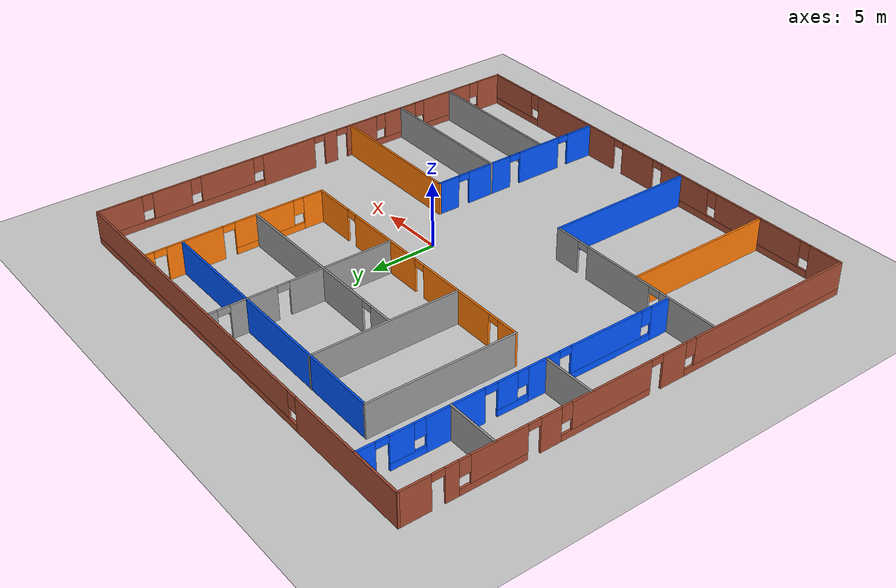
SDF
<sdf version="1.6">
 <world name="default">
  <plugin name="Welcome to Udacity s World!" filename="libsteve.so"/>
  <light name="sun" type="directional">
   <pose>0 0 10 0 -0 0</pose>
   <diffuse>0.8 0.8 0.8 1</diffuse>
   <specular>0.2 0.2 0.2 1</specular>
   <attenuation>
    <range>1000</range>
    <constant>0.9</constant>
    <linear>0.01</linear>
    <quadratic>0.001</quadratic>
   </attenuation>
   <direction>-0.5 0.1 -0.9</direction>
  </light>
  <model name="ground_plane">
   <static>1</static>
   <link name="link">
    <collision name="collision">
     <geometry><plane><normal>0 0 1</normal><size>100 100</size></plane></geometry>
     <surface>
      <contact><collide_bitmask>65535</collide_bitmask></contact>
      <friction><ode><mu>100</mu><mu2>50</mu2></ode></friction>
     </surface>
    </collision>
    <visual name="visual">
     <cast_shadows>0</cast_shadows>
     <geometry><plane><normal>0 0 1</normal><size>100 100</size></plane></geometry>
     <material>
      <script><uri>file://media/materials/scripts/gazebo.material</uri><name>Gazebo/Grey</name></script>
     </material>
    </visual>
   </link>
  </model>
  <gravity>0 0 -9.8</gravity>
  <magnetic_field>6e-06 2.3e-05 -4.2e-05</magnetic_field>
  <atmosphere type="adiabatic"/>
  <physics name="default_physics" default="0" type="ode">
   <max_step_size>0.001</max_step_size>
   <real_time_factor>1</real_time_factor>
   <real_time_update_rate>1000</real_time_update_rate>
  </physics>
  <scene><ambient>0.4 0.4 0.4 1</ambient><background>0.7 0.7 0.7 1</background><shadows>1</shadows></scene>
  <spherical_coordinates>
   <surface_model>EARTH_WGS84</surface_model>
   <latitude_deg>0</latitude_deg>
   <longitude_deg>0</longitude_deg>
   <elevation>0</elevation>
   <heading_deg>0</heading_deg>
  </spherical_coordinates>
  <model name="mybuilding">
   <pose>-3.17483 0.2831 0 0 -0 0</pose>
   <link name="Wall_0">
    <pose>-0.032167 17.425 0 0 -0 0.001673</pose>
    <visual name="Wall_0_Visual_0">
     <pose>-12.5646 0 1.25 0 -0 0</pose>
     <geometry><box><size>9.77748 0.15 2.5</size></box></geometry>
     <material>
      <script><uri>file://media/materials/scripts/gazebo.material</uri><name>Gazebo/Bricks</name></script>
      <ambient>1 1 1 1</ambient>
     </material>
     <meta><layer>0</layer></meta>
    </visual>
    <collision name="Wall_0_Collision_0">
     <geometry><box><size>9.77748 0.15 2.5</size></box></geometry>
     <pose>-12.5646 0 1.25 0 -0 0</pose>
    </collision>
    <visual name="Wall_0_Visual_1">
     <pose>4.88874 0 0.25 0 -0 0</pose>
     <geometry><box><size>25.1293 0.15 0.5</size></box></geometry>
     <material>
      <script><uri>file://media/materials/scripts/gazebo.material</uri><name>Gazebo/Bricks</name></script>
      <ambient>1 1 1 1</ambient>
     </material>
     <meta><layer>0</layer></meta>
    </visual>
    <collision name="Wall_0_Collision_1">
     <geometry><box><size>25.1293 0.15 0.5</size></box></geometry>
     <pose>4.88874 0 0.25 0 -0 0</pose>
    </collision>
    <visual name="Wall_0_Visual_2">
     <pose>5.28874 0 1.5 0 -0 0</pose>
     <geometry><box><size>24.3293 0.15 2</size></box></geometry>
     <material>
      <script><uri>file://media/materials/scripts/gazebo.material</uri><name>Gazebo/Bricks</name></script>
      <ambient>1 1 1 1</ambient>
     </material>
     <meta><layer>0</layer></meta>
    </visual>
    <collision name="Wall_0_Collision_2">
     <geometry><box><size>24.3293 0.15 2</size></box></geometry>
     <pose>5.28874 0 1.5 0 -0 0</pose>
    </collision>
    <visual name="Wall_0_Visual_3">
     <pose>-7.2759 0 1.9 0 -0 0</pose>
     <geometry><box><size>0.8 0.15 1.2</size></box></geometry>
     <material>
      <script><uri>file://media/materials/scripts/gazebo.material</uri><name>Gazebo/Bricks</name></script>
      <ambient>1 1 1 1</ambient>
     </material>
     <meta><layer>0</layer></meta>
    </visual>
    <collision name="Wall_0_Collision_3">
     <geometry><box><size>0.8 0.15 1.2</size></box></geometry>
     <pose>-7.2759 0 1.9 0 -0 0</pose>
    </collision>
   </link>
   <link name="Wall_11">
    <pose>-0.003817 -17.4439 0 0 -0 0.000584</pose>
    <visual name="Wall_11_Visual_0">
     <pose>-16.2159 0 1.25 0 -0 0</pose>
     <geometry><box><size>2.53083 0.15 2.5</size></box></geometry>
     <material>
      <script><uri>file://media/materials/scripts/gazebo.material</uri><name>Gazebo/Bricks</name></script>
      <ambient>1 1 1 1</ambient>
     </material>
     <meta><layer>0</layer></meta>
    </visual>
    <collision name="Wall_11_Collision_0">
     <geometry><box><size>2.53083 0.15 2.5</size></box></geometry>
     <pose>-16.2159 0 1.25 0 -0 0</pose>
    </collision>
    <visual name="Wall_11_Visual_1">
     <pose>1.13173 0 1.25 0 -0 0</pose>
     <geometry><box><size>3.14674 0.15 2.5</size></box></geometry>
     <material>
      <script><uri>file://media/materials/scripts/gazebo.material</uri><name>Gazebo/Bricks</name></script>
      <ambient>1 1 1 1</ambient>
     </material>
     <meta><layer>0</layer></meta>
    </visual>
    <collision name="Wall_11_Collision_1">
     <geometry><box><size>3.14674 0.15 2.5</size></box></geometry>
     <pose>1.13173 0 1.25 0 -0 0</pose>
    </collision>
    <visual name="Wall_11_Visual_2">
     <pose>7.9258 0 1.25 0 -0 0</pose>
     <geometry><box><size>8.64142 0.15 2.5</size></box></geometry>
     <material>
      <script><uri>file://media/materials/scripts/gazebo.material</uri><name>Gazebo/Bricks</name></script>
      <ambient>1 1 1 1</ambient>
     </material>
     <meta><layer>0</layer></meta>
    </visual>
    <collision name="Wall_11_Collision_2">
     <geometry><box><size>8.64142 0.15 2.5</size></box></geometry>
     <pose>7.9258 0 1.25 0 -0 0</pose>
    </collision>
    <visual name="Wall_11_Visual_3">
     <pose>-8.14608 0 0.25 0 -0 0</pose>
     <geometry><box><size>13.6089 0.15 0.5</size></box></geometry>
     <material>
      <script><uri>file://media/materials/scripts/gazebo.material</uri><name>Gazebo/Bricks</name></script>
      <ambient>1 1 1 1</ambient>
     </material>
     <meta><layer>0</layer></meta>
    </visual>
    <collision name="Wall_11_Collision_3">
     <geometry><box><size>13.6089 0.15 0.5</size></box></geometry>
     <pose>-8.14608 0 0.25 0 -0 0</pose>
    </collision>
    <visual name="Wall_11_Visual_4">
     <pose>14.8639 0 0.25 0 -0 0</pose>
     <geometry><box><size>5.23484 0.15 0.5</size></box></geometry>
     <material>
      <script><uri>file://media/materials/scripts/gazebo.material</uri><name>Gazebo/Bricks</name></script>
      <ambient>1 1 1 1</ambient>
     </material>
     <meta><layer>0</layer></meta>
    </visual>
    <collision name="Wall_11_Collision_4">
     <geometry><box><size>5.23484 0.15 0.5</size></box></geometry>
     <pose>14.8639 0 0.25 0 -0 0</pose>
    </collision>
    <visual name="Wall_11_Visual_5">
     <pose>-10.4098 0 1.5 0 -0 0</pose>
     <geometry><box><size>7.48141 0.15 2</size></box></geometry>
     <material>
      <script><uri>file://media/materials/scripts/gazebo.material</uri><name>Gazebo/Bricks</name></script>
      <ambient>1 1 1 1</ambient>
     </material>
     <meta><layer>0</layer></meta>
    </visual>
    <collision name="Wall_11_Collision_5">
     <geometry><box><size>7.48141 0.15 2</size></box></geometry>
     <pose>-10.4098 0 1.5 0 -0 0</pose>
    </collision>
    <visual name="Wall_11_Visual_6">
     <pose>-3.60538 0 1.5 0 -0 0</pose>
     <geometry><box><size>4.52747 0.15 2</size></box></geometry>
     <material>
      <script><uri>file://media/materials/scripts/gazebo.material</uri><name>Gazebo/Bricks</name></script>
      <ambient>1 1 1 1</ambient>
     </material>
     <meta><layer>0</layer></meta>
    </visual>
    <collision name="Wall_11_Collision_6">
     <geometry><box><size>4.52747 0.15 2</size></box></geometry>
     <pose>-3.60538 0 1.5 0 -0 0</pose>
    </collision>
    <visual name="Wall_11_Visual_7">
     <pose>-3.60538 0 1.5 0 -0 0</pose>
     <geometry><box><size>4.52747 0.15 2</size></box></geometry>
     <material>
      <script><uri>file://media/materials/scripts/gazebo.material</uri><name>Gazebo/Bricks</name></script>
      <ambient>1 1 1 1</ambient>
     </material>
     <meta><layer>0</layer></meta>
    </visual>
    <collision name="Wall_11_Collision_7">
     <geometry><box><size>4.52747 0.15 2</size></box></geometry>
     <pose>-3.60538 0 1.5 0 -0 0</pose>
    </collision>
    <visual name="Wall_11_Visual_8">
     <pose>15.2639 0 1.5 0 -0 0</pose>
     <geometry><box><size>4.43484 0.15 2</size></box></geometry>
     <material>
      <script><uri>file://media/materials/scripts/gazebo.material</uri><name>Gazebo/Bricks</name></script>
      <ambient>1 1 1 1</ambient>
     </material>
     <meta><layer>0</layer></meta>
    </visual>
    <collision name="Wall_11_Collision_8">
     <geometry><box><size>4.43484 0.15 2</size></box></geometry>
     <pose>15.2639 0 1.5 0 -0 0</pose>
    </collision>
    <visual name="Wall_11_Visual_9">
     <pose>-14.5505 0 1.9 0 -0 0</pose>
     <geometry><box><size>0.8 0.15 1.2</size></box></geometry>
     <material>
      <script><uri>file://media/materials/scripts/gazebo.material</uri><name>Gazebo/Bricks</name></script>
      <ambient>1 1 1 1</ambient>
     </material>
     <meta><layer>0</layer></meta>
    </visual>
    <collision name="Wall_11_Collision_9">
     <geometry><box><size>0.8 0.15 1.2</size></box></geometry>
     <pose>-14.5505 0 1.9 0 -0 0</pose>
    </collision>
    <visual name="Wall_11_Visual_10">
     <pose>12.6465 0 1.9 0 -0 0</pose>
     <geometry><box><size>0.8 0.15 1.2</size></box></geometry>
     <material>
      <script><uri>file://media/materials/scripts/gazebo.material</uri><name>Gazebo/Bricks</name></script>
      <ambient>1 1 1 1</ambient>
     </material>
     <meta><layer>0</layer></meta>
    </visual>
    <collision name="Wall_11_Collision_10">
     <geometry><box><size>0.8 0.15 1.2</size></box></geometry>
     <pose>12.6465 0 1.9 0 -0 0</pose>
    </collision>
    <visual name="Wall_11_Visual_11">
     <pose>-6.26911 0 1.9 0 -0 0</pose>
     <geometry><box><size>0.8 0.15 1.2</size></box></geometry>
     <material>
      <script><uri>file://media/materials/scripts/gazebo.material</uri><name>Gazebo/Bricks</name></script>
      <ambient>1 1 1 1</ambient>
     </material>
     <meta><layer>0</layer></meta>
    </visual>
    <collision name="Wall_11_Collision_11">
     <geometry><box><size>0.8 0.15 1.2</size></box></geometry>
     <pose>-6.26911 0 1.9 0 -0 0</pose>
    </collision>
    <visual name="Wall_11_Visual_12">
     <pose>3.1551 0 2.25 0 -0 0</pose>
     <geometry><box><size>0.9 0.15 0.5</size></box></geometry>
     <material>
      <script><uri>file://media/materials/scripts/gazebo.material</uri><name>Gazebo/Bricks</name></script>
      <ambient>1 1 1 1</ambient>
     </material>
     <meta><layer>0</layer></meta>
    </visual>
    <collision name="Wall_11_Collision_12">
     <geometry><box><size>0.9 0.15 0.5</size></box></geometry>
     <pose>3.1551 0 2.25 0 -0 0</pose>
    </collision>
    <visual name="Wall_11_Visual_13">
     <pose>-0.89164 0 2.25 0 -0 0</pose>
     <geometry><box><size>0.9 0.15 0.5</size></box></geometry>
     <material>
      <script><uri>file://media/materials/scripts/gazebo.material</uri><name>Gazebo/Bricks</name></script>
      <ambient>1 1 1 1</ambient>
     </material>
     <meta><layer>0</layer></meta>
    </visual>
    <collision name="Wall_11_Collision_13">
     <geometry><box><size>0.9 0.15 0.5</size></box></geometry>
     <pose>-0.89164 0 2.25 0 -0 0</pose>
    </collision>
    <visual name="Wall_11_Visual_14">
     <pose>-0.89164 0 2.25 0 -0 0</pose>
     <geometry><box><size>0.9 0.15 0.5</size></box></geometry>
     <material>
      <script><uri>file://media/materials/scripts/gazebo.material</uri><name>Gazebo/Bricks</name></script>
      <ambient>1 1 1 1</ambient>
     </material>
     <meta><layer>0</layer></meta>
    </visual>
    <collision name="Wall_11_Collision_14">
     <geometry><box><size>0.9 0.15 0.5</size></box></geometry>
     <pose>-0.89164 0 2.25 0 -0 0</pose>
    </collision>
   </link>
   <link name="Wall_13">
    <pose>-10.3069 -5.93049 0 0 -0 0</pose>
    <visual name="Wall_13_Visual_0">
     <pose>-4.77531 0 1.25 0 -0 0</pose>
     <geometry><box><size>4.69938 0.15 2.5</size></box></geometry>
     <material>
      <script><uri>file://media/materials/scripts/gazebo.material</uri><name>Gazebo/Grey</name></script>
      <ambient>1 1 1 1</ambient>
     </material>
     <meta><layer>0</layer></meta>
    </visual>
    <collision name="Wall_13_Collision_0">
     <geometry><box><size>4.69938 0.15 2.5</size></box></geometry>
     <pose>-4.77531 0 1.25 0 -0 0</pose>
    </collision>
    <visual name="Wall_13_Visual_1">
     <pose>1.31815 0 1.25 0 -0 0</pose>
     <geometry><box><size>5.68753 0.15 2.5</size></box></geometry>
     <material>
      <script><uri>file://media/materials/scripts/gazebo.material</uri><name>Gazebo/Grey</name></script>
      <ambient>1 1 1 1</ambient>
     </material>
     <meta><layer>0</layer></meta>
    </visual>
    <collision name="Wall_13_Collision_1">
     <geometry><box><size>5.68753 0.15 2.5</size></box></geometry>
     <pose>1.31815 0 1.25 0 -0 0</pose>
    </collision>
    <visual name="Wall_13_Visual_2">
     <pose>6.09346 0 1.25 0 -0 0</pose>
     <geometry><box><size>2.06308 0.15 2.5</size></box></geometry>
     <material>
      <script><uri>file://media/materials/scripts/gazebo.material</uri><name>Gazebo/Grey</name></script>
      <ambient>1 1 1 1</ambient>
     </material>
     <meta><layer>0</layer></meta>
    </visual>
    <collision name="Wall_13_Collision_2">
     <geometry><box><size>2.06308 0.15 2.5</size></box></geometry>
     <pose>6.09346 0 1.25 0 -0 0</pose>
    </collision>
    <visual name="Wall_13_Visual_3">
     <pose>-1.97562 0 2.25 0 -0 0</pose>
     <geometry><box><size>0.9 0.15 0.5</size></box></geometry>
     <material>
      <script><uri>file://media/materials/scripts/gazebo.material</uri><name>Gazebo/Grey</name></script>
      <ambient>1 1 1 1</ambient>
     </material>
     <meta><layer>0</layer></meta>
    </visual>
    <collision name="Wall_13_Collision_3">
     <geometry><box><size>0.9 0.15 0.5</size></box></geometry>
     <pose>-1.97562 0 2.25 0 -0 0</pose>
    </collision>
    <visual name="Wall_13_Visual_4">
     <pose>4.61192 0 2.25 0 -0 0</pose>
     <geometry><box><size>0.9 0.15 0.5</size></box></geometry>
     <material>
      <script><uri>file://media/materials/scripts/gazebo.material</uri><name>Gazebo/Grey</name></script>
      <ambient>1 1 1 1</ambient>
     </material>
     <meta><layer>0</layer></meta>
    </visual>
    <collision name="Wall_13_Collision_4">
     <geometry><box><size>0.9 0.15 0.5</size></box></geometry>
     <pose>4.61192 0 2.25 0 -0 0</pose>
    </collision>
   </link>
   <link name="Wall_14">
    <collision name="Wall_14_Collision">
     <geometry><box><size>11.5 0.15 2.5</size></box></geometry>
     <pose>0 0 1.25 0 -0 0</pose>
    </collision>
    <visual name="Wall_14_Visual">
     <pose>0 0 1.25 0 -0 0</pose>
     <geometry><box><size>11.5 0.15 2.5</size></box></geometry>
     <material>
      <script><uri>file://media/materials/scripts/gazebo.material</uri><name>Gazebo/Grey</name></script>
      <ambient>0 0.333333 1 1</ambient>
     </material>
     <meta><layer>0</layer></meta>
    </visual>
    <pose>-3.2569 -11.6055 0 0 0 -1.5708</pose>
   </link>
   <link name="Wall_16">
    <collision name="Wall_16_Collision">
     <geometry><box><size>11.5 0.15 2.5</size></box></geometry>
     <pose>0 0 1.25 0 -0 0</pose>
    </collision>
    <visual name="Wall_16_Visual">
     <pose>0 0 1.25 0 -0 0</pose>
     <geometry><box><size>11.5 0.15 2.5</size></box></geometry>
     <material>
      <script><uri>file://media/materials/scripts/gazebo.material</uri><name>Gazebo/Grey</name></script>
      <ambient>0.996078 0.47451 0.0196078 1</ambient>
     </material>
     <meta><layer>0</layer></meta>
    </visual>
    <pose>-10.6102 -11.6055 0 0 0 -1.5708</pose>
   </link>
   <link name="Wall_18">
    <pose>-13.5315 5.73081 0 0 -0 1.5708</pose>
    <visual name="Wall_18_Visual_0">
     <pose>-10.919 0 1.25 0 -0 0</pose>
     <geometry><box><size>1.61207 0.15 2.5</size></box></geometry>
     <material>
      <script><uri>file://media/materials/scripts/gazebo.material</uri><name>Gazebo/Grey</name></script>
      <ambient>0 0.333333 1 1</ambient>
     </material>
     <meta><layer>0</layer></meta>
    </visual>
    <collision name="Wall_18_Collision_0">
     <geometry><box><size>1.61207 0.15 2.5</size></box></geometry>
     <pose>-10.919 0 1.25 0 -0 0</pose>
    </collision>
    <visual name="Wall_18_Visual_1">
     <pose>-1.52186 0 1.25 0 -0 0</pose>
     <geometry><box><size>2.37107 0.15 2.5</size></box></geometry>
     <material>
      <script><uri>file://media/materials/scripts/gazebo.material</uri><name>Gazebo/Grey</name></script>
      <ambient>0 0.333333 1 1</ambient>
     </material>
     <meta><layer>0</layer></meta>
    </visual>
    <collision name="Wall_18_Collision_1">
     <geometry><box><size>2.37107 0.15 2.5</size></box></geometry>
     <pose>-1.52186 0 1.25 0 -0 0</pose>
    </collision>
    <visual name="Wall_18_Visual_2">
     <pose>4.9225 0 1.25 0 -0 0</pose>
     <geometry><box><size>4.15508 0.15 2.5</size></box></geometry>
     <material>
      <script><uri>file://media/materials/scripts/gazebo.material</uri><name>Gazebo/Grey</name></script>
      <ambient>0 0.333333 1 1</ambient>
     </material>
     <meta><layer>0</layer></meta>
    </visual>
    <collision name="Wall_18_Collision_2">
     <geometry><box><size>4.15508 0.15 2.5</size></box></geometry>
     <pose>4.9225 0 1.25 0 -0 0</pose>
    </collision>
    <visual name="Wall_18_Visual_3">
     <pose>11.0493 0 1.25 0 -0 0</pose>
     <geometry><box><size>1.35144 0.15 2.5</size></box></geometry>
     <material>
      <script><uri>file://media/materials/scripts/gazebo.material</uri><name>Gazebo/Grey</name></script>
      <ambient>0 0.333333 1 1</ambient>
     </material>
     <meta><layer>0</layer></meta>
    </visual>
    <collision name="Wall_18_Collision_3">
     <geometry><box><size>1.35144 0.15 2.5</size></box></geometry>
     <pose>11.0493 0 1.25 0 -0 0</pose>
    </collision>
    <visual name="Wall_18_Visual_4">
     <pose>-6.86016 0 0.25 0 -0 0</pose>
     <geometry><box><size>6.50554 0.15 0.5</size></box></geometry>
     <material>
      <script><uri>file://media/materials/scripts/gazebo.material</uri><name>Gazebo/Grey</name></script>
      <ambient>0 0.333333 1 1</ambient>
     </material>
     <meta><layer>0</layer></meta>
    </visual>
    <collision name="Wall_18_Collision_4">
     <geometry><box><size>6.50554 0.15 0.5</size></box></geometry>
     <pose>-6.86016 0 0.25 0 -0 0</pose>
    </collision>
    <visual name="Wall_18_Visual_5">
     <pose>0.804316 0 0.25 0 -0 0</pose>
     <geometry><box><size>2.28128 0.15 0.5</size></box></geometry>
     <material>
      <script><uri>file://media/materials/scripts/gazebo.material</uri><name>Gazebo/Grey</name></script>
      <ambient>0 0.333333 1 1</ambient>
     </material>
     <meta><layer>0</layer></meta>
    </visual>
    <collision name="Wall_18_Collision_5">
     <geometry><box><size>2.28128 0.15 0.5</size></box></geometry>
     <pose>0.804316 0 0.25 0 -0 0</pose>
    </collision>
    <visual name="Wall_18_Visual_6">
     <pose>8.2368 0 0.25 0 -0 0</pose>
     <geometry><box><size>2.47352 0.15 0.5</size></box></geometry>
     <material>
      <script><uri>file://media/materials/scripts/gazebo.material</uri><name>Gazebo/Grey</name></script>
      <ambient>0 0.333333 1 1</ambient>
     </material>
     <meta><layer>0</layer></meta>
    </visual>
    <collision name="Wall_18_Collision_6">
     <geometry><box><size>2.47352 0.15 0.5</size></box></geometry>
     <pose>8.2368 0 0.25 0 -0 0</pose>
    </collision>
    <visual name="Wall_18_Visual_7">
     <pose>-6.46016 0 1.5 0 -0 0</pose>
     <geometry><box><size>5.70554 0.15 2</size></box></geometry>
     <material>
      <script><uri>file://media/materials/scripts/gazebo.material</uri><name>Gazebo/Grey</name></script>
      <ambient>0 0.333333 1 1</ambient>
     </material>
     <meta><layer>0</layer></meta>
    </visual>
    <collision name="Wall_18_Collision_7">
     <geometry><box><size>5.70554 0.15 2</size></box></geometry>
     <pose>-6.46016 0 1.5 0 -0 0</pose>
    </collision>
    <visual name="Wall_18_Visual_8">
     <pose>-6.46016 0 1.5 0 -0 0</pose>
     <geometry><box><size>5.70554 0.15 2</size></box></geometry>
     <material>
      <script><uri>file://media/materials/scripts/gazebo.material</uri><name>Gazebo/Grey</name></script>
      <ambient>0 0.333333 1 1</ambient>
     </material>
     <meta><layer>0</layer></meta>
    </visual>
    <collision name="Wall_18_Collision_8">
     <geometry><box><size>5.70554 0.15 2</size></box></geometry>
     <pose>-6.46016 0 1.5 0 -0 0</pose>
    </collision>
    <visual name="Wall_18_Visual_9">
     <pose>1.20432 0 1.5 0 -0 0</pose>
     <geometry><box><size>1.48128 0.15 2</size></box></geometry>
     <material>
      <script><uri>file://media/materials/scripts/gazebo.material</uri><name>Gazebo/Grey</name></script>
      <ambient>0 0.333333 1 1</ambient>
     </material>
     <meta><layer>0</layer></meta>
    </visual>
    <collision name="Wall_18_Collision_9">
     <geometry><box><size>1.48128 0.15 2</size></box></geometry>
     <pose>1.20432 0 1.5 0 -0 0</pose>
    </collision>
    <visual name="Wall_18_Visual_10">
     <pose>1.20432 0 1.5 0 -0 0</pose>
     <geometry><box><size>1.48128 0.15 2</size></box></geometry>
     <material>
      <script><uri>file://media/materials/scripts/gazebo.material</uri><name>Gazebo/Grey</name></script>
      <ambient>0 0.333333 1 1</ambient>
     </material>
     <meta><layer>0</layer></meta>
    </visual>
    <collision name="Wall_18_Collision_10">
     <geometry><box><size>1.48128 0.15 2</size></box></geometry>
     <pose>1.20432 0 1.5 0 -0 0</pose>
    </collision>
    <visual name="Wall_18_Visual_11">
     <pose>8.6368 0 1.5 0 -0 0</pose>
     <geometry><box><size>1.67352 0.15 2</size></box></geometry>
     <material>
      <script><uri>file://media/materials/scripts/gazebo.material</uri><name>Gazebo/Grey</name></script>
      <ambient>0 0.333333 1 1</ambient>
     </material>
     <meta><layer>0</layer></meta>
    </visual>
    <collision name="Wall_18_Collision_11">
     <geometry><box><size>1.67352 0.15 2</size></box></geometry>
     <pose>8.6368 0 1.5 0 -0 0</pose>
    </collision>
    <visual name="Wall_18_Visual_12">
     <pose>-9.71293 0 1.9 0 -0 0</pose>
     <geometry><box><size>0.8 0.15 1.2</size></box></geometry>
     <material>
      <script><uri>file://media/materials/scripts/gazebo.material</uri><name>Gazebo/Grey</name></script>
      <ambient>0 0.333333 1 1</ambient>
     </material>
     <meta><layer>0</layer></meta>
    </visual>
    <collision name="Wall_18_Collision_12">
     <geometry><box><size>0.8 0.15 1.2</size></box></geometry>
     <pose>-9.71293 0 1.9 0 -0 0</pose>
    </collision>
    <visual name="Wall_18_Visual_13">
     <pose>0.063676 0 1.9 0 -0 0</pose>
     <geometry><box><size>0.8 0.15 1.2</size></box></geometry>
     <material>
      <script><uri>file://media/materials/scripts/gazebo.material</uri><name>Gazebo/Grey</name></script>
      <ambient>0 0.333333 1 1</ambient>
     </material>
     <meta><layer>0</layer></meta>
    </visual>
    <collision name="Wall_18_Collision_13">
     <geometry><box><size>0.8 0.15 1.2</size></box></geometry>
     <pose>0.063676 0 1.9 0 -0 0</pose>
    </collision>
    <visual name="Wall_18_Visual_14">
     <pose>7.40004 0 1.9 0 -0 0</pose>
     <geometry><box><size>0.8 0.15 1.2</size></box></geometry>
     <material>
      <script><uri>file://media/materials/scripts/gazebo.material</uri><name>Gazebo/Grey</name></script>
      <ambient>0 0.333333 1 1</ambient>
     </material>
     <meta><layer>0</layer></meta>
    </visual>
    <collision name="Wall_18_Collision_14">
     <geometry><box><size>0.8 0.15 1.2</size></box></geometry>
     <pose>7.40004 0 1.9 0 -0 0</pose>
    </collision>
    <visual name="Wall_18_Visual_15">
     <pose>-3.15739 0 2.25 0 -0 0</pose>
     <geometry><box><size>0.9 0.15 0.5</size></box></geometry>
     <material>
      <script><uri>file://media/materials/scripts/gazebo.material</uri><name>Gazebo/Grey</name></script>
      <ambient>0 0.333333 1 1</ambient>
     </material>
     <meta><layer>0</layer></meta>
    </visual>
    <collision name="Wall_18_Collision_15">
     <geometry><box><size>0.9 0.15 0.5</size></box></geometry>
     <pose>-3.15739 0 2.25 0 -0 0</pose>
    </collision>
    <visual name="Wall_18_Visual_16">
     <pose>-3.15739 0 2.25 0 -0 0</pose>
     <geometry><box><size>0.9 0.15 0.5</size></box></geometry>
     <material>
      <script><uri>file://media/materials/scripts/gazebo.material</uri><name>Gazebo/Grey</name></script>
      <ambient>0 0.333333 1 1</ambient>
     </material>
     <meta><layer>0</layer></meta>
    </visual>
    <collision name="Wall_18_Collision_16">
     <geometry><box><size>0.9 0.15 0.5</size></box></geometry>
     <pose>-3.15739 0 2.25 0 -0 0</pose>
    </collision>
    <visual name="Wall_18_Visual_17">
     <pose>2.39496 0 2.25 0 -0 0</pose>
     <geometry><box><size>0.9 0.15 0.5</size></box></geometry>
     <material>
      <script><uri>file://media/materials/scripts/gazebo.material</uri><name>Gazebo/Grey</name></script>
      <ambient>0 0.333333 1 1</ambient>
     </material>
     <meta><layer>0</layer></meta>
    </visual>
    <collision name="Wall_18_Collision_17">
     <geometry><box><size>0.9 0.15 0.5</size></box></geometry>
     <pose>2.39496 0 2.25 0 -0 0</pose>
    </collision>
    <visual name="Wall_18_Visual_18">
     <pose>2.39496 0 2.25 0 -0 0</pose>
     <geometry><box><size>0.9 0.15 0.5</size></box></geometry>
     <material>
      <script><uri>file://media/materials/scripts/gazebo.material</uri><name>Gazebo/Grey</name></script>
      <ambient>0 0.333333 1 1</ambient>
     </material>
     <meta><layer>0</layer></meta>
    </visual>
    <collision name="Wall_18_Collision_18">
     <geometry><box><size>0.9 0.15 0.5</size></box></geometry>
     <pose>2.39496 0 2.25 0 -0 0</pose>
    </collision>
    <visual name="Wall_18_Visual_19">
     <pose>9.92356 0 2.25 0 -0 0</pose>
     <geometry><box><size>0.9 0.15 0.5</size></box></geometry>
     <material>
      <script><uri>file://media/materials/scripts/gazebo.material</uri><name>Gazebo/Grey</name></script>
      <ambient>0 0.333333 1 1</ambient>
     </material>
     <meta><layer>0</layer></meta>
    </visual>
    <collision name="Wall_18_Collision_19">
     <geometry><box><size>0.9 0.15 0.5</size></box></geometry>
     <pose>9.92356 0 2.25 0 -0 0</pose>
    </collision>
   </link>
   <link name="Wall_20">
    <pose>6.31065 -10.25 0 0 -0 1.5708</pose>
    <visual name="Wall_20_Visual_0">
     <pose>-5.98664 0 1.25 0 -0 0</pose>
     <geometry><box><size>2.27671 0.15 2.5</size></box></geometry>
     <material>
      <script><uri>file://media/materials/scripts/gazebo.material</uri><name>Gazebo/Grey</name></script>
      <ambient>0 0.333333 1 1</ambient>
     </material>
     <meta><layer>0</layer></meta>
    </visual>
    <collision name="Wall_20_Collision_0">
     <geometry><box><size>2.27671 0.15 2.5</size></box></geometry>
     <pose>-5.98664 0 1.25 0 -0 0</pose>
    </collision>
    <visual name="Wall_20_Visual_1">
     <pose>-2.09265 0 1.25 0 -0 0</pose>
     <geometry><box><size>3.71127 0.15 2.5</size></box></geometry>
     <material>
      <script><uri>file://media/materials/scripts/gazebo.material</uri><name>Gazebo/Grey</name></script>
      <ambient>0 0.333333 1 1</ambient>
     </material>
     <meta><layer>0</layer></meta>
    </visual>
    <collision name="Wall_20_Collision_1">
     <geometry><box><size>3.71127 0.15 2.5</size></box></geometry>
     <pose>-2.09265 0 1.25 0 -0 0</pose>
    </collision>
    <visual name="Wall_20_Visual_2">
     <pose>2.56568 0 1.25 0 -0 0</pose>
     <geometry><box><size>3.80538 0.15 2.5</size></box></geometry>
     <material>
      <script><uri>file://media/materials/scripts/gazebo.material</uri><name>Gazebo/Grey</name></script>
      <ambient>0 0.333333 1 1</ambient>
     </material>
     <meta><layer>0</layer></meta>
    </visual>
    <collision name="Wall_20_Collision_2">
     <geometry><box><size>3.80538 0.15 2.5</size></box></geometry>
     <pose>2.56568 0 1.25 0 -0 0</pose>
    </collision>
    <visual name="Wall_20_Visual_3">
     <pose>6.24668 0 1.25 0 -0 0</pose>
     <geometry><box><size>1.75663 0.15 2.5</size></box></geometry>
     <material>
      <script><uri>file://media/materials/scripts/gazebo.material</uri><name>Gazebo/Grey</name></script>
      <ambient>0 0.333333 1 1</ambient>
     </material>
     <meta><layer>0</layer></meta>
    </visual>
    <collision name="Wall_20_Collision_3">
     <geometry><box><size>1.75663 0.15 2.5</size></box></geometry>
     <pose>6.24668 0 1.25 0 -0 0</pose>
    </collision>
    <visual name="Wall_20_Visual_4">
     <pose>-4.39829 0 2.25 0 -0 0</pose>
     <geometry><box><size>0.9 0.15 0.5</size></box></geometry>
     <material>
      <script><uri>file://media/materials/scripts/gazebo.material</uri><name>Gazebo/Grey</name></script>
      <ambient>0 0.333333 1 1</ambient>
     </material>
     <meta><layer>0</layer></meta>
    </visual>
    <collision name="Wall_20_Collision_4">
     <geometry><box><size>0.9 0.15 0.5</size></box></geometry>
     <pose>-4.39829 0 2.25 0 -0 0</pose>
    </collision>
    <visual name="Wall_20_Visual_5">
     <pose>0.212986 0 2.25 0 -0 0</pose>
     <geometry><box><size>0.9 0.15 0.5</size></box></geometry>
     <material>
      <script><uri>file://media/materials/scripts/gazebo.material</uri><name>Gazebo/Grey</name></script>
      <ambient>0 0.333333 1 1</ambient>
     </material>
     <meta><layer>0</layer></meta>
    </visual>
    <collision name="Wall_20_Collision_5">
     <geometry><box><size>0.9 0.15 0.5</size></box></geometry>
     <pose>0.212986 0 2.25 0 -0 0</pose>
    </collision>
    <visual name="Wall_20_Visual_6">
     <pose>4.91837 0 2.25 0 -0 0</pose>
     <geometry><box><size>0.9 0.15 0.5</size></box></geometry>
     <material>
      <script><uri>file://media/materials/scripts/gazebo.material</uri><name>Gazebo/Grey</name></script>
      <ambient>0 0.333333 1 1</ambient>
     </material>
     <meta><layer>0</layer></meta>
    </visual>
    <collision name="Wall_20_Collision_6">
     <geometry><box><size>0.9 0.15 0.5</size></box></geometry>
     <pose>4.91837 0 2.25 0 -0 0</pose>
    </collision>
   </link>
   <link name="Wall_21">
    <collision name="Wall_21_Collision">
     <geometry><box><size>11.25 0.15 2.5</size></box></geometry>
     <pose>0 0 1.25 0 -0 0</pose>
    </collision>
    <visual name="Wall_21_Visual">
     <pose>0 0 1.25 0 -0 0</pose>
     <geometry><box><size>11.25 0.15 2.5</size></box></geometry>
     <material>
      <script><uri>file://media/materials/scripts/gazebo.material</uri><name>Gazebo/Grey</name></script>
      <ambient>0.996078 0.47451 0.0196078 1</ambient>
     </material>
     <meta><layer>0</layer></meta>
    </visual>
    <pose>11.8606 -3.19998 0 0 -0 0</pose>
   </link>
   <link name="Wall_23">
    <collision name="Wall_23_Collision">
     <geometry><box><size>11.25 0.15 2.5</size></box></geometry>
     <pose>0 0 1.25 0 -0 0</pose>
    </collision>
    <visual name="Wall_23_Visual">
     <pose>0 0 1.25 0 -0 0</pose>
     <geometry><box><size>11.25 0.15 2.5</size></box></geometry>
     <material>
      <script><uri>file://media/materials/scripts/gazebo.material</uri><name>Gazebo/Grey</name></script>
      <ambient>1 1 1 1</ambient>
     </material>
     <meta><layer>0</layer></meta>
    </visual>
    <pose>11.8606 -7.84879 0 0 -0 0</pose>
   </link>
   <link name="Wall_25">
    <collision name="Wall_25_Collision">
     <geometry><box><size>11 0.15 2.5</size></box></geometry>
     <pose>0 0 1.25 0 -0 0</pose>
    </collision>
    <visual name="Wall_25_Visual">
     <pose>0 0 1.25 0 -0 0</pose>
     <geometry><box><size>11 0.15 2.5</size></box></geometry>
     <material>
      <script><uri>file://media/materials/scripts/gazebo.material</uri><name>Gazebo/Grey</name></script>
      <ambient>1 1 1 1</ambient>
     </material>
     <meta><layer>0</layer></meta>
    </visual>
    <pose>11.8292 -12.5276 0 0 -0 0</pose>
   </link>
   <link name="Wall_29">
    <collision name="Wall_29_Collision">
     <geometry><box><size>4 0.15 2.5</size></box></geometry>
     <pose>0 0 1.25 0 -0 0</pose>
    </collision>
    <visual name="Wall_29_Visual">
     <pose>0 0 1.25 0 -0 0</pose>
     <geometry><box><size>4 0.15 2.5</size></box></geometry>
     <material>
      <script><uri>file://media/materials/scripts/gazebo.material</uri><name>Gazebo/Grey</name></script>
      <ambient>1 1 1 1</ambient>
     </material>
     <meta><layer>0</layer></meta>
    </visual>
    <pose>-15.435 10.9591 0 0 -0 0</pose>
   </link>
   <link name="Wall_31">
    <collision name="Wall_31_Collision">
     <geometry><box><size>4 0.15 2.5</size></box></geometry>
     <pose>0 0 1.25 0 -0 0</pose>
    </collision>
    <visual name="Wall_31_Visual">
     <pose>0 0 1.25 0 -0 0</pose>
     <geometry><box><size>4 0.15 2.5</size></box></geometry>
     <material>
      <script><uri>file://media/materials/scripts/gazebo.material</uri><name>Gazebo/Grey</name></script>
      <ambient>1 1 1 1</ambient>
     </material>
     <meta><layer>0</layer></meta>
    </visual>
    <pose>-15.435 4.00381 0 0 -0 0</pose>
   </link>
   <link name="Wall_35">
    <pose>0.006793 3.83302 0 0 -0 0</pose>
    <visual name="Wall_35_Visual_0">
     <pose>-9.77473 0 1.25 0 -0 0</pose>
     <geometry><box><size>1.70054 0.15 2.5</size></box></geometry>
     <material>
      <script><uri>file://media/materials/scripts/gazebo.material</uri><name>Gazebo/Grey</name></script>
      <ambient>0.996078 0.47451 0.0196078 1</ambient>
     </material>
     <meta><layer>0</layer></meta>
    </visual>
    <collision name="Wall_35_Collision_0">
     <geometry><box><size>1.70054 0.15 2.5</size></box></geometry>
     <pose>-9.77473 0 1.25 0 -0 0</pose>
    </collision>
    <visual name="Wall_35_Visual_1">
     <pose>-4.71016 0 1.25 0 -0 0</pose>
     <geometry><box><size>6.62861 0.15 2.5</size></box></geometry>
     <material>
      <script><uri>file://media/materials/scripts/gazebo.material</uri><name>Gazebo/Grey</name></script>
      <ambient>0.996078 0.47451 0.0196078 1</ambient>
     </material>
     <meta><layer>0</layer></meta>
    </visual>
    <collision name="Wall_35_Collision_1">
     <geometry><box><size>6.62861 0.15 2.5</size></box></geometry>
     <pose>-4.71016 0 1.25 0 -0 0</pose>
    </collision>
    <visual name="Wall_35_Visual_2">
     <pose>2.9412 0 1.25 0 -0 0</pose>
     <geometry><box><size>6.87411 0.15 2.5</size></box></geometry>
     <material>
      <script><uri>file://media/materials/scripts/gazebo.material</uri><name>Gazebo/Grey</name></script>
      <ambient>0.996078 0.47451 0.0196078 1</ambient>
     </material>
     <meta><layer>0</layer></meta>
    </visual>
    <collision name="Wall_35_Collision_2">
     <geometry><box><size>6.87411 0.15 2.5</size></box></geometry>
     <pose>2.9412 0 1.25 0 -0 0</pose>
    </collision>
    <visual name="Wall_35_Visual_3">
     <pose>8.95163 0 1.25 0 -0 0</pose>
     <geometry><box><size>3.34675 0.15 2.5</size></box></geometry>
     <material>
      <script><uri>file://media/materials/scripts/gazebo.material</uri><name>Gazebo/Grey</name></script>
      <ambient>0.996078 0.47451 0.0196078 1</ambient>
     </material>
     <meta><layer>0</layer></meta>
    </visual>
    <collision name="Wall_35_Collision_3">
     <geometry><box><size>3.34675 0.15 2.5</size></box></geometry>
     <pose>8.95163 0 1.25 0 -0 0</pose>
    </collision>
    <visual name="Wall_35_Visual_4">
     <pose>-8.47446 0 2.25 0 -0 0</pose>
     <geometry><box><size>0.9 0.15 0.5</size></box></geometry>
     <material>
      <script><uri>file://media/materials/scripts/gazebo.material</uri><name>Gazebo/Grey</name></script>
      <ambient>0.996078 0.47451 0.0196078 1</ambient>
     </material>
     <meta><layer>0</layer></meta>
    </visual>
    <collision name="Wall_35_Collision_4">
     <geometry><box><size>0.9 0.15 0.5</size></box></geometry>
     <pose>-8.47446 0 2.25 0 -0 0</pose>
    </collision>
    <visual name="Wall_35_Visual_5">
     <pose>-0.945851 0 2.25 0 -0 0</pose>
     <geometry><box><size>0.9 0.15 0.5</size></box></geometry>
     <material>
      <script><uri>file://media/materials/scripts/gazebo.material</uri><name>Gazebo/Grey</name></script>
      <ambient>0.996078 0.47451 0.0196078 1</ambient>
     </material>
     <meta><layer>0</layer></meta>
    </visual>
    <collision name="Wall_35_Collision_5">
     <geometry><box><size>0.9 0.15 0.5</size></box></geometry>
     <pose>-0.945851 0 2.25 0 -0 0</pose>
    </collision>
    <visual name="Wall_35_Visual_6">
     <pose>6.82825 0 2.25 0 -0 0</pose>
     <geometry><box><size>0.9 0.15 0.5</size></box></geometry>
     <material>
      <script><uri>file://media/materials/scripts/gazebo.material</uri><name>Gazebo/Grey</name></script>
      <ambient>0.996078 0.47451 0.0196078 1</ambient>
     </material>
     <meta><layer>0</layer></meta>
    </visual>
    <collision name="Wall_35_Collision_6">
     <geometry><box><size>0.9 0.15 0.5</size></box></geometry>
     <pose>6.82825 0 2.25 0 -0 0</pose>
    </collision>
   </link>
   <link name="Wall_37">
    <pose>10.5568 10.608 0 0 -0 1.5708</pose>
    <visual name="Wall_37_Visual_0">
     <pose>-6.03177 0 1.25 0 -0 0</pose>
     <geometry><box><size>1.63647 0.15 2.5</size></box></geometry>
     <material>
      <script><uri>file://media/materials/scripts/gazebo.material</uri><name>Gazebo/Grey</name></script>
      <ambient>0.996078 0.47451 0.0196078 1</ambient>
     </material>
     <meta><layer>0</layer></meta>
    </visual>
    <collision name="Wall_37_Collision_0">
     <geometry><box><size>1.63647 0.15 2.5</size></box></geometry>
     <pose>-6.03177 0 1.25 0 -0 0</pose>
    </collision>
    <visual name="Wall_37_Visual_1">
     <pose>3.17289 0 1.25 0 -0 0</pose>
     <geometry><box><size>4.16443 0.15 2.5</size></box></geometry>
     <material>
      <script><uri>file://media/materials/scripts/gazebo.material</uri><name>Gazebo/Grey</name></script>
      <ambient>0.996078 0.47451 0.0196078 1</ambient>
     </material>
     <meta><layer>0</layer></meta>
    </visual>
    <collision name="Wall_37_Collision_1">
     <geometry><box><size>4.16443 0.15 2.5</size></box></geometry>
     <pose>3.17289 0 1.25 0 -0 0</pose>
    </collision>
    <visual name="Wall_37_Visual_2">
     <pose>6.50255 0 1.25 0 -0 0</pose>
     <geometry><box><size>0.694895 0.15 2.5</size></box></geometry>
     <material>
      <script><uri>file://media/materials/scripts/gazebo.material</uri><name>Gazebo/Grey</name></script>
      <ambient>0.996078 0.47451 0.0196078 1</ambient>
     </material>
     <meta><layer>0</layer></meta>
    </visual>
    <collision name="Wall_37_Collision_2">
     <geometry><box><size>0.694895 0.15 2.5</size></box></geometry>
     <pose>6.50255 0 1.25 0 -0 0</pose>
    </collision>
    <visual name="Wall_37_Visual_3">
     <pose>-2.51143 0 0.25 0 -0 0</pose>
     <geometry><box><size>5.40421 0.15 0.5</size></box></geometry>
     <material>
      <script><uri>file://media/materials/scripts/gazebo.material</uri><name>Gazebo/Grey</name></script>
      <ambient>0.996078 0.47451 0.0196078 1</ambient>
     </material>
     <meta><layer>0</layer></meta>
    </visual>
    <collision name="Wall_37_Collision_3">
     <geometry><box><size>5.40421 0.15 0.5</size></box></geometry>
     <pose>-2.51143 0 0.25 0 -0 0</pose>
    </collision>
    <visual name="Wall_37_Visual_4">
     <pose>-2.11143 0 1.5 0 -0 0</pose>
     <geometry><box><size>4.60421 0.15 2</size></box></geometry>
     <material>
      <script><uri>file://media/materials/scripts/gazebo.material</uri><name>Gazebo/Grey</name></script>
      <ambient>0.996078 0.47451 0.0196078 1</ambient>
     </material>
     <meta><layer>0</layer></meta>
    </visual>
    <collision name="Wall_37_Collision_4">
     <geometry><box><size>4.60421 0.15 2</size></box></geometry>
     <pose>-2.11143 0 1.5 0 -0 0</pose>
    </collision>
    <visual name="Wall_37_Visual_5">
     <pose>-4.81353 0 1.9 0 -0 0</pose>
     <geometry><box><size>0.8 0.15 1.2</size></box></geometry>
     <material>
      <script><uri>file://media/materials/scripts/gazebo.material</uri><name>Gazebo/Grey</name></script>
      <ambient>0.996078 0.47451 0.0196078 1</ambient>
     </material>
     <meta><layer>0</layer></meta>
    </visual>
    <collision name="Wall_37_Collision_5">
     <geometry><box><size>0.8 0.15 1.2</size></box></geometry>
     <pose>-4.81353 0 1.9 0 -0 0</pose>
    </collision>
    <visual name="Wall_37_Visual_6">
     <pose>5.7051 0 2.25 0 -0 0</pose>
     <geometry><box><size>0.9 0.15 0.5</size></box></geometry>
     <material>
      <script><uri>file://media/materials/scripts/gazebo.material</uri><name>Gazebo/Grey</name></script>
      <ambient>0.996078 0.47451 0.0196078 1</ambient>
     </material>
     <meta><layer>0</layer></meta>
    </visual>
    <collision name="Wall_37_Collision_6">
     <geometry><box><size>0.9 0.15 0.5</size></box></geometry>
     <pose>5.7051 0 2.25 0 -0 0</pose>
    </collision>
    <visual name="Wall_37_Visual_7">
     <pose>0.640675 0 2.25 0 -0 0</pose>
     <geometry><box><size>0.9 0.15 0.5</size></box></geometry>
     <material>
      <script><uri>file://media/materials/scripts/gazebo.material</uri><name>Gazebo/Grey</name></script>
      <ambient>0.996078 0.47451 0.0196078 1</ambient>
     </material>
     <meta><layer>0</layer></meta>
    </visual>
    <collision name="Wall_37_Collision_7">
     <geometry><box><size>0.9 0.15 0.5</size></box></geometry>
     <pose>0.640675 0 2.25 0 -0 0</pose>
    </collision>
   </link>
   <link name="Wall_39">
    <collision name="Wall_39_Collision">
     <geometry><box><size>11 0.15 2.5</size></box></geometry>
     <pose>0 0 1.25 0 -0 0</pose>
    </collision>
    <visual name="Wall_39_Visual">
     <pose>0 0 1.25 0 -0 0</pose>
     <geometry><box><size>11 0.15 2.5</size></box></geometry>
     <material>
      <script><uri>file://media/materials/scripts/gazebo.material</uri><name>Gazebo/Grey</name></script>
      <ambient>1 1 1 1</ambient>
     </material>
     <meta><layer>0</layer></meta>
    </visual>
    <pose>-10.5432 9.25802 0 0 -0 1.5708</pose>
   </link>
   <link name="Wall_40">
    <collision name="Wall_40_Collision">
     <geometry><box><size>13 0.15 2.5</size></box></geometry>
     <pose>0 0 1.25 0 -0 0</pose>
    </collision>
    <visual name="Wall_40_Visual">
     <pose>0 0 1.25 0 -0 0</pose>
     <geometry><box><size>13 0.15 2.5</size></box></geometry>
     <material>
      <script><uri>file://media/materials/scripts/gazebo.material</uri><name>Gazebo/Grey</name></script>
      <ambient>0 0.333333 1 1</ambient>
     </material>
     <meta><layer>0</layer></meta>
    </visual>
    <pose>-4.11821 14.683 0 0 -0 0</pose>
   </link>
   <link name="Wall_41">
    <pose>2.30679 15.983 0 0 -0 1.5708</pose>
    <visual name="Wall_41_Visual_0">
     <pose>-0.747448 0 1.25 0 -0 0</pose>
     <geometry><box><size>1.2551 0.15 2.5</size></box></geometry>
     <material>
      <script><uri>file://media/materials/scripts/gazebo.material</uri><name>Gazebo/Grey</name></script>
      <ambient>1 1 1 1</ambient>
     </material>
     <meta><layer>0</layer></meta>
    </visual>
    <collision name="Wall_41_Collision_0">
     <geometry><box><size>1.2551 0.15 2.5</size></box></geometry>
     <pose>-0.747448 0 1.25 0 -0 0</pose>
    </collision>
    <visual name="Wall_41_Visual_1">
     <pose>1.07755 0 1.25 0 -0 0</pose>
     <geometry><box><size>0.594895 0.15 2.5</size></box></geometry>
     <material>
      <script><uri>file://media/materials/scripts/gazebo.material</uri><name>Gazebo/Grey</name></script>
      <ambient>1 1 1 1</ambient>
     </material>
     <meta><layer>0</layer></meta>
    </visual>
    <collision name="Wall_41_Collision_1">
     <geometry><box><size>0.594895 0.15 2.5</size></box></geometry>
     <pose>1.07755 0 1.25 0 -0 0</pose>
    </collision>
    <visual name="Wall_41_Visual_2">
     <pose>0.330105 0 2.25 0 -0 0</pose>
     <geometry><box><size>0.9 0.15 0.5</size></box></geometry>
     <material>
      <script><uri>file://media/materials/scripts/gazebo.material</uri><name>Gazebo/Grey</name></script>
      <ambient>1 1 1 1</ambient>
     </material>
     <meta><layer>0</layer></meta>
    </visual>
    <collision name="Wall_41_Collision_2">
     <geometry><box><size>0.9 0.15 0.5</size></box></geometry>
     <pose>0.330105 0 2.25 0 -0 0</pose>
    </collision>
   </link>
   <link name="Wall_43">
    <collision name="Wall_43_Collision">
     <geometry><box><size>8.25 0.15 2.5</size></box></geometry>
     <pose>0 0 1.25 0 -0 0</pose>
    </collision>
    <visual name="Wall_43_Visual">
     <pose>0 0 1.25 0 -0 0</pose>
     <geometry><box><size>8.25 0.15 2.5</size></box></geometry>
     <material>
      <script><uri>file://media/materials/scripts/gazebo.material</uri><name>Gazebo/Grey</name></script>
      <ambient>0 0.333333 1 1</ambient>
     </material>
     <meta><layer>0</layer></meta>
    </visual>
    <pose>6.35679 14.683 0 0 -0 0</pose>
   </link>
   <link name="Wall_45">
    <pose>2.30679 9.25802 0 0 0 -1.5708</pose>
    <visual name="Wall_45_Visual_0">
     <pose>-4.3795 0 1.25 0 -0 0</pose>
     <geometry><box><size>2.241 0.15 2.5</size></box></geometry>
     <material>
      <script><uri>file://media/materials/scripts/gazebo.material</uri><name>Gazebo/Grey</name></script>
      <ambient>1 1 1 1</ambient>
     </material>
     <meta><layer>0</layer></meta>
    </visual>
    <collision name="Wall_45_Collision_0">
     <geometry><box><size>2.241 0.15 2.5</size></box></geometry>
     <pose>-4.3795 0 1.25 0 -0 0</pose>
    </collision>
    <visual name="Wall_45_Visual_1">
     <pose>1.5705 0 1.25 0 -0 0</pose>
     <geometry><box><size>7.859 0.15 2.5</size></box></geometry>
     <material>
      <script><uri>file://media/materials/scripts/gazebo.material</uri><name>Gazebo/Grey</name></script>
      <ambient>1 1 1 1</ambient>
     </material>
     <meta><layer>0</layer></meta>
    </visual>
    <collision name="Wall_45_Collision_1">
     <geometry><box><size>7.859 0.15 2.5</size></box></geometry>
     <pose>1.5705 0 1.25 0 -0 0</pose>
    </collision>
    <visual name="Wall_45_Visual_2">
     <pose>-2.809 0 2.25 0 -0 0</pose>
     <geometry><box><size>0.9 0.15 0.5</size></box></geometry>
     <material>
      <script><uri>file://media/materials/scripts/gazebo.material</uri><name>Gazebo/Grey</name></script>
      <ambient>1 1 1 1</ambient>
     </material>
     <meta><layer>0</layer></meta>
    </visual>
    <collision name="Wall_45_Collision_2">
     <geometry><box><size>0.9 0.15 0.5</size></box></geometry>
     <pose>-2.809 0 2.25 0 -0 0</pose>
    </collision>
   </link>
   <link name="Wall_47">
    <collision name="Wall_47_Collision">
     <geometry><box><size>11 0.15 2.5</size></box></geometry>
     <pose>0 0 1.25 0 -0 0</pose>
    </collision>
    <visual name="Wall_47_Visual">
     <pose>0 0 1.25 0 -0 0</pose>
     <geometry><box><size>11 0.15 2.5</size></box></geometry>
     <material>
      <script><uri>file://media/materials/scripts/gazebo.material</uri><name>Gazebo/Grey</name></script>
      <ambient>1 1 1 1</ambient>
     </material>
     <meta><layer>0</layer></meta>
    </visual>
    <pose>-4.94212 9.2883 0 0 0 -1.5708</pose>
   </link>
   <link name="Wall_49">
    <pose>2.80199 9.06684 0 0 -0 0</pose>
    <visual name="Wall_49_Visual_0">
     <pose>-6.77635 0 1.25 0 -0 0</pose>
     <geometry><box><size>1.8973 0.15 2.5</size></box></geometry>
     <material>
      <script><uri>file://media/materials/scripts/gazebo.material</uri><name>Gazebo/Grey</name></script>
      <ambient>1 1 1 1</ambient>
     </material>
     <meta><layer>0</layer></meta>
    </visual>
    <collision name="Wall_49_Collision_0">
     <geometry><box><size>1.8973 0.15 2.5</size></box></geometry>
     <pose>-6.77635 0 1.25 0 -0 0</pose>
    </collision>
    <visual name="Wall_49_Visual_1">
     <pose>1.39865 0 1.25 0 -0 0</pose>
     <geometry><box><size>12.6527 0.15 2.5</size></box></geometry>
     <material>
      <script><uri>file://media/materials/scripts/gazebo.material</uri><name>Gazebo/Grey</name></script>
      <ambient>1 1 1 1</ambient>
     </material>
     <meta><layer>0</layer></meta>
    </visual>
    <collision name="Wall_49_Collision_1">
     <geometry><box><size>12.6527 0.15 2.5</size></box></geometry>
     <pose>1.39865 0 1.25 0 -0 0</pose>
    </collision>
    <visual name="Wall_49_Visual_2">
     <pose>-5.3777 0 2.25 0 -0 0</pose>
     <geometry><box><size>0.9 0.15 0.5</size></box></geometry>
     <material>
      <script><uri>file://media/materials/scripts/gazebo.material</uri><name>Gazebo/Grey</name></script>
      <ambient>1 1 1 1</ambient>
     </material>
     <meta><layer>0</layer></meta>
    </visual>
    <collision name="Wall_49_Collision_2">
     <geometry><box><size>0.9 0.15 0.5</size></box></geometry>
     <pose>-5.3777 0 2.25 0 -0 0</pose>
    </collision>
   </link>
   <link name="Wall_7">
    <pose>17.4025 -0.008779 0 0 -0 1.5708</pose>
    <visual name="Wall_7_Visual_0">
     <pose>-16.4134 0 1.25 0 -0 0</pose>
     <geometry><box><size>2.17315 0.15 2.5</size></box></geometry>
     <material>
      <script><uri>file://media/materials/scripts/gazebo.material</uri><name>Gazebo/Bricks</name></script>
      <ambient>1 1 1 1</ambient>
     </material>
     <meta><layer>0</layer></meta>
    </visual>
    <collision name="Wall_7_Collision_0">
     <geometry><box><size>2.17315 0.15 2.5</size></box></geometry>
     <pose>-16.4134 0 1.25 0 -0 0</pose>
    </collision>
    <visual name="Wall_7_Visual_1">
     <pose>-1.32327 0 1.25 0 -0 0</pose>
     <geometry><box><size>1.07626 0.15 2.5</size></box></geometry>
     <material>
      <script><uri>file://media/materials/scripts/gazebo.material</uri><name>Gazebo/Bricks</name></script>
      <ambient>1 1 1 1</ambient>
     </material>
     <meta><layer>0</layer></meta>
    </visual>
    <collision name="Wall_7_Collision_1">
     <geometry><box><size>1.07626 0.15 2.5</size></box></geometry>
     <pose>-1.32327 0 1.25 0 -0 0</pose>
    </collision>
    <visual name="Wall_7_Visual_2">
     <pose>2.32236 0 1.25 0 -0 0</pose>
     <geometry><box><size>4.41499 0.15 2.5</size></box></geometry>
     <material>
      <script><uri>file://media/materials/scripts/gazebo.material</uri><name>Gazebo/Bricks</name></script>
      <ambient>1 1 1 1</ambient>
     </material>
     <meta><layer>0</layer></meta>
    </visual>
    <collision name="Wall_7_Collision_2">
     <geometry><box><size>4.41499 0.15 2.5</size></box></geometry>
     <pose>2.32236 0 1.25 0 -0 0</pose>
    </collision>
    <visual name="Wall_7_Visual_3">
     <pose>-9.04412 0 0.25 0 -0 0</pose>
     <geometry><box><size>12.5655 0.15 0.5</size></box></geometry>
     <material>
      <script><uri>file://media/materials/scripts/gazebo.material</uri><name>Gazebo/Bricks</name></script>
      <ambient>1 1 1 1</ambient>
     </material>
     <meta><layer>0</layer></meta>
    </visual>
    <collision name="Wall_7_Collision_3">
     <geometry><box><size>12.5655 0.15 0.5</size></box></geometry>
     <pose>-9.04412 0 0.25 0 -0 0</pose>
    </collision>
    <visual name="Wall_7_Visual_4">
     <pose>11.0149 0 0.25 0 -0 0</pose>
     <geometry><box><size>12.9701 0.15 0.5</size></box></geometry>
     <material>
      <script><uri>file://media/materials/scripts/gazebo.material</uri><name>Gazebo/Bricks</name></script>
      <ambient>1 1 1 1</ambient>
     </material>
     <meta><layer>0</layer></meta>
    </visual>
    <collision name="Wall_7_Collision_4">
     <geometry><box><size>12.9701 0.15 0.5</size></box></geometry>
     <pose>11.0149 0 0.25 0 -0 0</pose>
    </collision>
    <visual name="Wall_7_Visual_5">
     <pose>-12.2448 0 1.5 0 -0 0</pose>
     <geometry><box><size>4.56413 0.15 2</size></box></geometry>
     <material>
      <script><uri>file://media/materials/scripts/gazebo.material</uri><name>Gazebo/Bricks</name></script>
      <ambient>1 1 1 1</ambient>
     </material>
     <meta><layer>0</layer></meta>
    </visual>
    <collision name="Wall_7_Collision_5">
     <geometry><box><size>4.56413 0.15 2</size></box></geometry>
     <pose>-12.2448 0 1.5 0 -0 0</pose>
    </collision>
    <visual name="Wall_7_Visual_6">
     <pose>-7.72762 0 1.5 0 -0 0</pose>
     <geometry><box><size>2.8702 0.15 2</size></box></geometry>
     <material>
      <script><uri>file://media/materials/scripts/gazebo.material</uri><name>Gazebo/Bricks</name></script>
      <ambient>1 1 1 1</ambient>
     </material>
     <meta><layer>0</layer></meta>
    </visual>
    <collision name="Wall_7_Collision_6">
     <geometry><box><size>2.8702 0.15 2</size></box></geometry>
     <pose>-7.72762 0 1.5 0 -0 0</pose>
    </collision>
    <visual name="Wall_7_Visual_7">
     <pose>-4.12696 0 1.5 0 -0 0</pose>
     <geometry><box><size>2.73112 0.15 2</size></box></geometry>
     <material>
      <script><uri>file://media/materials/scripts/gazebo.material</uri><name>Gazebo/Bricks</name></script>
      <ambient>1 1 1 1</ambient>
     </material>
     <meta><layer>0</layer></meta>
    </visual>
    <collision name="Wall_7_Collision_7">
     <geometry><box><size>2.73112 0.15 2</size></box></geometry>
     <pose>-4.12696 0 1.5 0 -0 0</pose>
    </collision>
    <visual name="Wall_7_Visual_8">
     <pose>-4.12696 0 1.5 0 -0 0</pose>
     <geometry><box><size>2.73112 0.15 2</size></box></geometry>
     <material>
      <script><uri>file://media/materials/scripts/gazebo.material</uri><name>Gazebo/Bricks</name></script>
      <ambient>1 1 1 1</ambient>
     </material>
     <meta><layer>0</layer></meta>
    </visual>
    <collision name="Wall_7_Collision_8">
     <geometry><box><size>2.73112 0.15 2</size></box></geometry>
     <pose>-4.12696 0 1.5 0 -0 0</pose>
    </collision>
    <visual name="Wall_7_Visual_9">
     <pose>7.47076 0 1.5 0 -0 0</pose>
     <geometry><box><size>4.28181 0.15 2</size></box></geometry>
     <material>
      <script><uri>file://media/materials/scripts/gazebo.material</uri><name>Gazebo/Bricks</name></script>
      <ambient>1 1 1 1</ambient>
     </material>
     <meta><layer>0</layer></meta>
    </visual>
    <collision name="Wall_7_Collision_9">
     <geometry><box><size>4.28181 0.15 2</size></box></geometry>
     <pose>7.47076 0 1.5 0 -0 0</pose>
    </collision>
    <visual name="Wall_7_Visual_10">
     <pose>11.8938 0 1.5 0 -0 0</pose>
     <geometry><box><size>2.9643 0.15 2</size></box></geometry>
     <material>
      <script><uri>file://media/materials/scripts/gazebo.material</uri><name>Gazebo/Bricks</name></script>
      <ambient>1 1 1 1</ambient>
     </material>
     <meta><layer>0</layer></meta>
    </visual>
    <collision name="Wall_7_Collision_10">
     <geometry><box><size>2.9643 0.15 2</size></box></geometry>
     <pose>11.8938 0 1.5 0 -0 0</pose>
    </collision>
    <visual name="Wall_7_Visual_11">
     <pose>15.838 0 1.5 0 -0 0</pose>
     <geometry><box><size>3.32403 0.15 2</size></box></geometry>
     <material>
      <script><uri>file://media/materials/scripts/gazebo.material</uri><name>Gazebo/Bricks</name></script>
      <ambient>1 1 1 1</ambient>
     </material>
     <meta><layer>0</layer></meta>
    </visual>
    <collision name="Wall_7_Collision_11">
     <geometry><box><size>3.32403 0.15 2</size></box></geometry>
     <pose>15.838 0 1.5 0 -0 0</pose>
    </collision>
    <visual name="Wall_7_Visual_12">
     <pose>-14.9268 0 1.9 0 -0 0</pose>
     <geometry><box><size>0.8 0.15 1.2</size></box></geometry>
     <material>
      <script><uri>file://media/materials/scripts/gazebo.material</uri><name>Gazebo/Bricks</name></script>
      <ambient>1 1 1 1</ambient>
     </material>
     <meta><layer>0</layer></meta>
    </visual>
    <collision name="Wall_7_Collision_12">
     <geometry><box><size>0.8 0.15 1.2</size></box></geometry>
     <pose>-14.9268 0 1.9 0 -0 0</pose>
    </collision>
    <visual name="Wall_7_Visual_13">
     <pose>4.92985 0 1.9 0 -0 0</pose>
     <geometry><box><size>0.8 0.15 1.2</size></box></geometry>
     <material>
      <script><uri>file://media/materials/scripts/gazebo.material</uri><name>Gazebo/Bricks</name></script>
      <ambient>1 1 1 1</ambient>
     </material>
     <meta><layer>0</layer></meta>
    </visual>
    <collision name="Wall_7_Collision_13">
     <geometry><box><size>0.8 0.15 1.2</size></box></geometry>
     <pose>4.92985 0 1.9 0 -0 0</pose>
    </collision>
    <visual name="Wall_7_Visual_14">
     <pose>-9.56272 0 1.9 0 -0 0</pose>
     <geometry><box><size>0.8 0.15 1.2</size></box></geometry>
     <material>
      <script><uri>file://media/materials/scripts/gazebo.material</uri><name>Gazebo/Bricks</name></script>
      <ambient>1 1 1 1</ambient>
     </material>
     <meta><layer>0</layer></meta>
    </visual>
    <collision name="Wall_7_Collision_14">
     <geometry><box><size>0.8 0.15 1.2</size></box></geometry>
     <pose>-9.56272 0 1.9 0 -0 0</pose>
    </collision>
    <visual name="Wall_7_Visual_15">
     <pose>-5.89252 0 1.9 0 -0 0</pose>
     <geometry><box><size>0.8 0.15 1.2</size></box></geometry>
     <material>
      <script><uri>file://media/materials/scripts/gazebo.material</uri><name>Gazebo/Bricks</name></script>
      <ambient>1 1 1 1</ambient>
     </material>
     <meta><layer>0</layer></meta>
    </visual>
    <collision name="Wall_7_Collision_15">
     <geometry><box><size>0.8 0.15 1.2</size></box></geometry>
     <pose>-5.89252 0 1.9 0 -0 0</pose>
    </collision>
    <visual name="Wall_7_Visual_16">
     <pose>10.0117 0 1.9 0 -0 0</pose>
     <geometry><box><size>0.8 0.15 1.2</size></box></geometry>
     <material>
      <script><uri>file://media/materials/scripts/gazebo.material</uri><name>Gazebo/Bricks</name></script>
      <ambient>1 1 1 1</ambient>
     </material>
     <meta><layer>0</layer></meta>
    </visual>
    <collision name="Wall_7_Collision_16">
     <geometry><box><size>0.8 0.15 1.2</size></box></geometry>
     <pose>10.0117 0 1.9 0 -0 0</pose>
    </collision>
    <visual name="Wall_7_Visual_17">
     <pose>13.776 0 1.9 0 -0 0</pose>
     <geometry><box><size>0.8 0.15 1.2</size></box></geometry>
     <material>
      <script><uri>file://media/materials/scripts/gazebo.material</uri><name>Gazebo/Bricks</name></script>
      <ambient>1 1 1 1</ambient>
     </material>
     <meta><layer>0</layer></meta>
    </visual>
    <collision name="Wall_7_Collision_17">
     <geometry><box><size>0.8 0.15 1.2</size></box></geometry>
     <pose>13.776 0 1.9 0 -0 0</pose>
    </collision>
    <visual name="Wall_7_Visual_18">
     <pose>-0.335138 0 2.25 0 -0 0</pose>
     <geometry><box><size>0.9 0.15 0.5</size></box></geometry>
     <material>
      <script><uri>file://media/materials/scripts/gazebo.material</uri><name>Gazebo/Bricks</name></script>
      <ambient>1 1 1 1</ambient>
     </material>
     <meta><layer>0</layer></meta>
    </visual>
    <collision name="Wall_7_Collision_18">
     <geometry><box><size>0.9 0.15 0.5</size></box></geometry>
     <pose>-0.335138 0 2.25 0 -0 0</pose>
    </collision>
    <visual name="Wall_7_Visual_19">
     <pose>-2.3114 0 2.25 0 -0 0</pose>
     <geometry><box><size>0.9 0.15 0.5</size></box></geometry>
     <material>
      <script><uri>file://media/materials/scripts/gazebo.material</uri><name>Gazebo/Bricks</name></script>
      <ambient>1 1 1 1</ambient>
     </material>
     <meta><layer>0</layer></meta>
    </visual>
    <collision name="Wall_7_Collision_19">
     <geometry><box><size>0.9 0.15 0.5</size></box></geometry>
     <pose>-2.3114 0 2.25 0 -0 0</pose>
    </collision>
    <visual name="Wall_7_Visual_20">
     <pose>-2.3114 0 2.25 0 -0 0</pose>
     <geometry><box><size>0.9 0.15 0.5</size></box></geometry>
     <material>
      <script><uri>file://media/materials/scripts/gazebo.material</uri><name>Gazebo/Bricks</name></script>
      <ambient>1 1 1 1</ambient>
     </material>
     <meta><layer>0</layer></meta>
    </visual>
    <collision name="Wall_7_Collision_20">
     <geometry><box><size>0.9 0.15 0.5</size></box></geometry>
     <pose>-2.3114 0 2.25 0 -0 0</pose>
    </collision>
   </link>
   <link name="Wall_9">
    <pose>-17.4102 -0.029118 0 0 0 -1.5708</pose>
    <visual name="Wall_9_Visual_0">
     <pose>-16.3933 0 1.25 0 -0 0</pose>
     <geometry><box><size>2.21348 0.15 2.5</size></box></geometry>
     <material>
      <script><uri>file://media/materials/scripts/gazebo.material</uri><name>Gazebo/Bricks</name></script>
      <ambient>1 1 1 1</ambient>
     </material>
     <meta><layer>0</layer></meta>
    </visual>
    <collision name="Wall_9_Collision_0">
     <geometry><box><size>2.21348 0.15 2.5</size></box></geometry>
     <pose>-16.3933 0 1.25 0 -0 0</pose>
    </collision>
    <visual name="Wall_9_Visual_1">
     <pose>-13.9323 0 1.25 0 -0 0</pose>
     <geometry><box><size>0.908389 0.15 2.5</size></box></geometry>
     <material>
      <script><uri>file://media/materials/scripts/gazebo.material</uri><name>Gazebo/Bricks</name></script>
      <ambient>1 1 1 1</ambient>
     </material>
     <meta><layer>0</layer></meta>
    </visual>
    <collision name="Wall_9_Collision_1">
     <geometry><box><size>0.908389 0.15 2.5</size></box></geometry>
     <pose>-13.9323 0 1.25 0 -0 0</pose>
    </collision>
    <visual name="Wall_9_Visual_2">
     <pose>-7.04224 0 1.25 0 -0 0</pose>
     <geometry><box><size>1.51351 0.15 2.5</size></box></geometry>
     <material>
      <script><uri>file://media/materials/scripts/gazebo.material</uri><name>Gazebo/Bricks</name></script>
      <ambient>1 1 1 1</ambient>
     </material>
     <meta><layer>0</layer></meta>
    </visual>
    <collision name="Wall_9_Collision_2">
     <geometry><box><size>1.51351 0.15 2.5</size></box></geometry>
     <pose>-7.04224 0 1.25 0 -0 0</pose>
    </collision>
    <visual name="Wall_9_Visual_3">
     <pose>2.47345 0 1.25 0 -0 0</pose>
     <geometry><box><size>1.91159 0.15 2.5</size></box></geometry>
     <material>
      <script><uri>file://media/materials/scripts/gazebo.material</uri><name>Gazebo/Bricks</name></script>
      <ambient>1 1 1 1</ambient>
     </material>
     <meta><layer>0</layer></meta>
    </visual>
    <collision name="Wall_9_Collision_3">
     <geometry><box><size>1.91159 0.15 2.5</size></box></geometry>
     <pose>2.47345 0 1.25 0 -0 0</pose>
    </collision>
    <visual name="Wall_9_Visual_4">
     <pose>-11.0886 0 0.25 0 -0 0</pose>
     <geometry><box><size>4.77914 0.15 0.5</size></box></geometry>
     <material>
      <script><uri>file://media/materials/scripts/gazebo.material</uri><name>Gazebo/Bricks</name></script>
      <ambient>1 1 1 1</ambient>
     </material>
     <meta><layer>0</layer></meta>
    </visual>
    <collision name="Wall_9_Collision_4">
     <geometry><box><size>4.77914 0.15 0.5</size></box></geometry>
     <pose>-11.0886 0 0.25 0 -0 0</pose>
    </collision>
    <visual name="Wall_9_Visual_5">
     <pose>-2.83391 0 0.25 0 -0 0</pose>
     <geometry><box><size>6.90314 0.15 0.5</size></box></geometry>
     <material>
      <script><uri>file://media/materials/scripts/gazebo.material</uri><name>Gazebo/Bricks</name></script>
      <ambient>1 1 1 1</ambient>
     </material>
     <meta><layer>0</layer></meta>
    </visual>
    <collision name="Wall_9_Collision_5">
     <geometry><box><size>6.90314 0.15 0.5</size></box></geometry>
     <pose>-2.83391 0 0.25 0 -0 0</pose>
    </collision>
    <visual name="Wall_9_Visual_6">
     <pose>10.4646 0 0.25 0 -0 0</pose>
     <geometry><box><size>14.0708 0.15 0.5</size></box></geometry>
     <material>
      <script><uri>file://media/materials/scripts/gazebo.material</uri><name>Gazebo/Bricks</name></script>
      <ambient>1 1 1 1</ambient>
     </material>
     <meta><layer>0</layer></meta>
    </visual>
    <collision name="Wall_9_Collision_6">
     <geometry><box><size>14.0708 0.15 0.5</size></box></geometry>
     <pose>10.4646 0 0.25 0 -0 0</pose>
    </collision>
    <visual name="Wall_9_Visual_7">
     <pose>-10.6886 0 1.5 0 -0 0</pose>
     <geometry><box><size>3.97914 0.15 2</size></box></geometry>
     <material>
      <script><uri>file://media/materials/scripts/gazebo.material</uri><name>Gazebo/Bricks</name></script>
      <ambient>1 1 1 1</ambient>
     </material>
     <meta><layer>0</layer></meta>
    </visual>
    <collision name="Wall_9_Collision_7">
     <geometry><box><size>3.97914 0.15 2</size></box></geometry>
     <pose>-10.6886 0 1.5 0 -0 0</pose>
    </collision>
    <visual name="Wall_9_Visual_8">
     <pose>-10.6886 0 1.5 0 -0 0</pose>
     <geometry><box><size>3.97914 0.15 2</size></box></geometry>
     <material>
      <script><uri>file://media/materials/scripts/gazebo.material</uri><name>Gazebo/Bricks</name></script>
      <ambient>1 1 1 1</ambient>
     </material>
     <meta><layer>0</layer></meta>
    </visual>
    <collision name="Wall_9_Collision_8">
     <geometry><box><size>3.97914 0.15 2</size></box></geometry>
     <pose>-10.6886 0 1.5 0 -0 0</pose>
    </collision>
    <visual name="Wall_9_Visual_9">
     <pose>-2.43391 0 1.5 0 -0 0</pose>
     <geometry><box><size>6.10314 0.15 2</size></box></geometry>
     <material>
      <script><uri>file://media/materials/scripts/gazebo.material</uri><name>Gazebo/Bricks</name></script>
      <ambient>1 1 1 1</ambient>
     </material>
     <meta><layer>0</layer></meta>
    </visual>
    <collision name="Wall_9_Collision_9">
     <geometry><box><size>6.10314 0.15 2</size></box></geometry>
     <pose>-2.43391 0 1.5 0 -0 0</pose>
    </collision>
    <visual name="Wall_9_Visual_10">
     <pose>-2.43391 0 1.5 0 -0 0</pose>
     <geometry><box><size>6.10314 0.15 2</size></box></geometry>
     <material>
      <script><uri>file://media/materials/scripts/gazebo.material</uri><name>Gazebo/Bricks</name></script>
      <ambient>1 1 1 1</ambient>
     </material>
     <meta><layer>0</layer></meta>
    </visual>
    <collision name="Wall_9_Collision_10">
     <geometry><box><size>6.10314 0.15 2</size></box></geometry>
     <pose>-2.43391 0 1.5 0 -0 0</pose>
    </collision>
    <visual name="Wall_9_Visual_11">
     <pose>10.8646 0 1.5 0 -0 0</pose>
     <geometry><box><size>13.2708 0.15 2</size></box></geometry>
     <material>
      <script><uri>file://media/materials/scripts/gazebo.material</uri><name>Gazebo/Bricks</name></script>
      <ambient>1 1 1 1</ambient>
     </material>
     <meta><layer>0</layer></meta>
    </visual>
    <collision name="Wall_9_Collision_11">
     <geometry><box><size>13.2708 0.15 2</size></box></geometry>
     <pose>10.8646 0 1.5 0 -0 0</pose>
    </collision>
    <visual name="Wall_9_Visual_12">
     <pose>-13.0781 0 1.9 0 -0 0</pose>
     <geometry><box><size>0.8 0.15 1.2</size></box></geometry>
     <material>
      <script><uri>file://media/materials/scripts/gazebo.material</uri><name>Gazebo/Bricks</name></script>
      <ambient>1 1 1 1</ambient>
     </material>
     <meta><layer>0</layer></meta>
    </visual>
    <collision name="Wall_9_Collision_12">
     <geometry><box><size>0.8 0.15 1.2</size></box></geometry>
     <pose>-13.0781 0 1.9 0 -0 0</pose>
    </collision>
    <visual name="Wall_9_Visual_13">
     <pose>-5.88548 0 1.9 0 -0 0</pose>
     <geometry><box><size>0.8 0.15 1.2</size></box></geometry>
     <material>
      <script><uri>file://media/materials/scripts/gazebo.material</uri><name>Gazebo/Bricks</name></script>
      <ambient>1 1 1 1</ambient>
     </material>
     <meta><layer>0</layer></meta>
    </visual>
    <collision name="Wall_9_Collision_13">
     <geometry><box><size>0.8 0.15 1.2</size></box></geometry>
     <pose>-5.88548 0 1.9 0 -0 0</pose>
    </collision>
    <visual name="Wall_9_Visual_14">
     <pose>3.82925 0 1.9 0 -0 0</pose>
     <geometry><box><size>0.8 0.15 1.2</size></box></geometry>
     <material>
      <script><uri>file://media/materials/scripts/gazebo.material</uri><name>Gazebo/Bricks</name></script>
      <ambient>1 1 1 1</ambient>
     </material>
     <meta><layer>0</layer></meta>
    </visual>
    <collision name="Wall_9_Collision_14">
     <geometry><box><size>0.8 0.15 1.2</size></box></geometry>
     <pose>3.82925 0 1.9 0 -0 0</pose>
    </collision>
    <visual name="Wall_9_Visual_15">
     <pose>-14.8365 0 2.25 0 -0 0</pose>
     <geometry><box><size>0.9 0.15 0.5</size></box></geometry>
     <material>
      <script><uri>file://media/materials/scripts/gazebo.material</uri><name>Gazebo/Bricks</name></script>
      <ambient>1 1 1 1</ambient>
     </material>
     <meta><layer>0</layer></meta>
    </visual>
    <collision name="Wall_9_Collision_15">
     <geometry><box><size>0.9 0.15 0.5</size></box></geometry>
     <pose>-14.8365 0 2.25 0 -0 0</pose>
    </collision>
    <visual name="Wall_9_Visual_16">
     <pose>-8.24899 0 2.25 0 -0 0</pose>
     <geometry><box><size>0.9 0.15 0.5</size></box></geometry>
     <material>
      <script><uri>file://media/materials/scripts/gazebo.material</uri><name>Gazebo/Bricks</name></script>
      <ambient>1 1 1 1</ambient>
     </material>
     <meta><layer>0</layer></meta>
    </visual>
    <collision name="Wall_9_Collision_16">
     <geometry><box><size>0.9 0.15 0.5</size></box></geometry>
     <pose>-8.24899 0 2.25 0 -0 0</pose>
    </collision>
    <visual name="Wall_9_Visual_17">
     <pose>-8.24899 0 2.25 0 -0 0</pose>
     <geometry><box><size>0.9 0.15 0.5</size></box></geometry>
     <material>
      <script><uri>file://media/materials/scripts/gazebo.material</uri><name>Gazebo/Bricks</name></script>
      <ambient>1 1 1 1</ambient>
     </material>
     <meta><layer>0</layer></meta>
    </visual>
    <collision name="Wall_9_Collision_17">
     <geometry><box><size>0.9 0.15 0.5</size></box></geometry>
     <pose>-8.24899 0 2.25 0 -0 0</pose>
    </collision>
    <visual name="Wall_9_Visual_18">
     <pose>1.06766 0 2.25 0 -0 0</pose>
     <geometry><box><size>0.9 0.15 0.5</size></box></geometry>
     <material>
      <script><uri>file://media/materials/scripts/gazebo.material</uri><name>Gazebo/Bricks</name></script>
      <ambient>1 1 1 1</ambient>
     </material>
     <meta><layer>0</layer></meta>
    </visual>
    <collision name="Wall_9_Collision_18">
     <geometry><box><size>0.9 0.15 0.5</size></box></geometry>
     <pose>1.06766 0 2.25 0 -0 0</pose>
    </collision>
    <visual name="Wall_9_Visual_19">
     <pose>1.06766 0 2.25 0 -0 0</pose>
     <geometry><box><size>0.9 0.15 0.5</size></box></geometry>
     <material>
      <script><uri>file://media/materials/scripts/gazebo.material</uri><name>Gazebo/Bricks</name></script>
      <ambient>1 1 1 1</ambient>
     </material>
     <meta><layer>0</layer></meta>
    </visual>
    <collision name="Wall_9_Collision_19">
     <geometry><box><size>0.9 0.15 0.5</size></box></geometry>
     <pose>1.06766 0 2.25 0 -0 0</pose>
    </collision>
   </link>
   <static>1</static>
  </model>
  <model name="my_ball">
   <link name="link">
    <inertial>
     <mass>0.1</mass>
     <inertia><ixx>0.1</ixx><ixy>0</ixy><ixz>0</ixz><iyy>0.1</iyy><iyz>0</iyz><izz>0.1</izz></inertia>
    </inertial>
    <visual name="visual">
     <geometry><sphere><radius>0.1</radius></sphere></geometry>
     <material>
      <script><name>Gazebo/Grey</name><uri>file://media/materials/scripts/gazebo.material</uri></script>
      <shader type="pixel"><normal_map>__default__</normal_map></shader>
      <ambient>1 1 1 1</ambient>
      <diffuse>1 1 1 1</diffuse>
      <specular>1 1 1 1</specular>
      <emissive>1 1 1 1</emissive>
     </material>
    </visual>
    <collision name="collision">
     <geometry><sphere><radius>0.1</radius></sphere></geometry>
     <surface>
      <friction>
       <ode><mu>1</mu><mu2>1</mu2><fdir1>0 0 0</fdir1><slip1>0</slip1><slip2>0</slip2></ode>
       <torsional>
        <coefficient>1</coefficient>
        <patch_radius>0</patch_radius>
        <surface_radius>0</surface_radius>
        <use_patch_radius>1</use_patch_radius>
        <ode><slip>0</slip></ode>
       </torsional>
      </friction>
      <bounce><restitution_coefficient>0</restitution_coefficient><threshold>1e+06</threshold></bounce>
      <contact>
       <collide_without_contact>0</collide_without_contact>
       <collide_without_contact_bitmask>1</collide_without_contact_bitmask>
       <collide_bitmask>1</collide_bitmask>
       <ode>
        <soft_cfm>0</soft_cfm>
        <soft_erp>0.2</soft_erp>
        <kp>1e+13</kp>
        <kd>1</kd>
        <max_vel>0.01</max_vel>
        <min_depth>0</min_depth>
       </ode>
       <bullet>
        <split_impulse>1</split_impulse>
        <split_impulse_penetration_threshold>-0.01</split_impulse_penetration_threshold>
        <soft_cfm>0</soft_cfm>
        <soft_erp>0.2</soft_erp>
        <kp>1e+13</kp>
        <kd>1</kd>
       </bullet>
      </contact>
     </surface>
    </collision>
   </link>
   <static>0</static>
   <pose>14.9105 2.0297 0.1 0 -0 0</pose>
  </model>
 </world>
</sdf>
